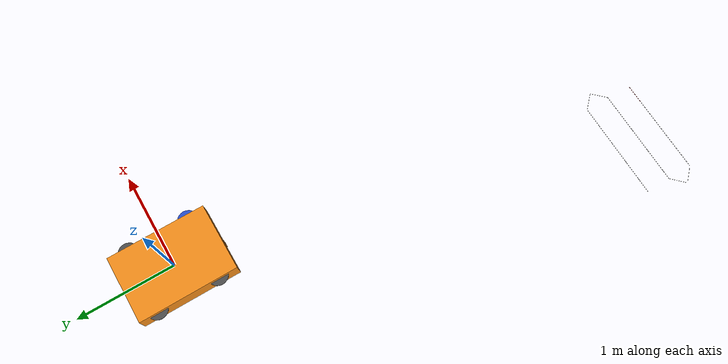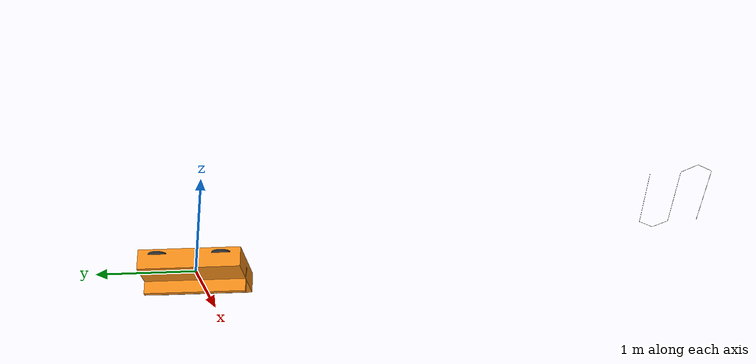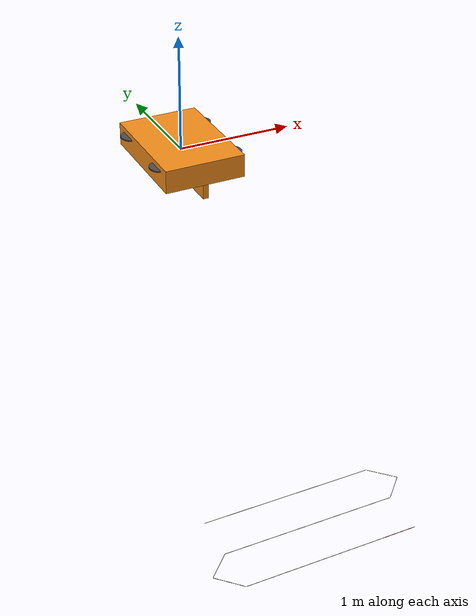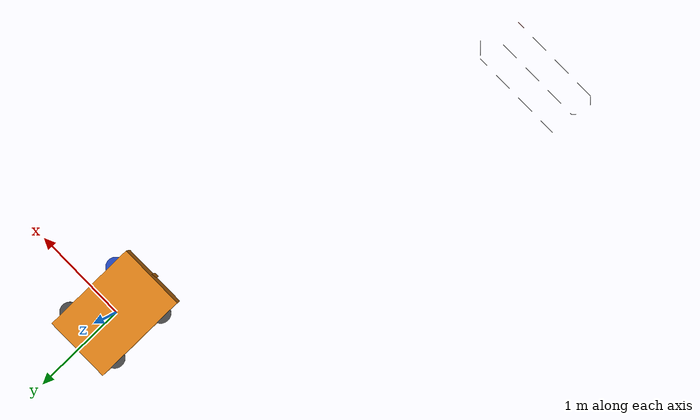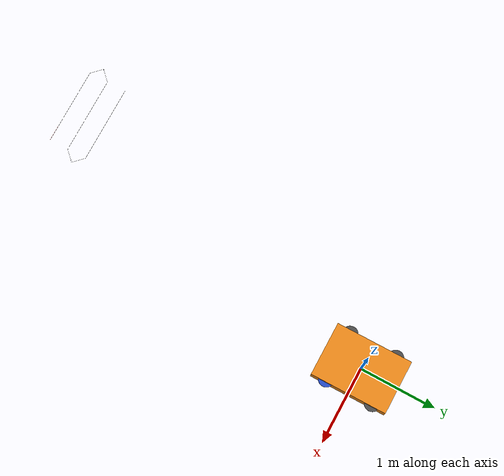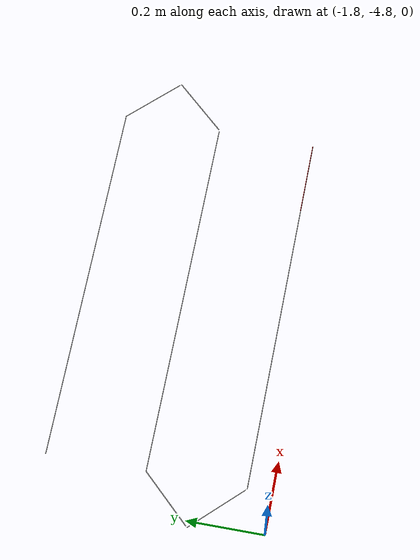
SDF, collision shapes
<?xml version='1.0'?>
<sdf version='1.5'>
  <model name='kitex_with_tether'>
    <include>
      <uri>model://kitex</uri>
    </include>
    <include>
      <uri>model://tether</uri>
    </include>
   </model>
</sdf>

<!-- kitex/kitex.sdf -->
<sdf version='1.6'>
	<model name='kitex'>
	<link name='base_link'>
		  <pose>0 0 0 0 -0 0</pose>
		  <inertial>
			<pose>0 0 -0.0 0 -0 0</pose>
			<mass>1.5</mass> <!-- [kg] -->
			<inertia> <!-- [kg/m²]-->
			  <ixx>0.15</ixx>
			  <ixy>0</ixy>
			  <ixz>0</ixz>
			  <iyy>0.05</iyy>
			  <iyz>0</iyz>
			  <izz>0.15</izz>
			</inertia>
		</inertial>
		<!-- TODO -->
		  <collision name='base_link_collision_wing'>
			<pose>0 0 -0.1 0 -0 0</pose>
			<geometry>
			  <box>
				<size>0.05 1 0.25</size>
			  </box>
			</geometry>
			<surface>
			  <contact>
				<ode>
				  <max_vel>10</max_vel>
				  <min_depth>0.01</min_depth>
				</ode>
			  </contact>
			</surface>
		  </collision>
		  <collision name='base_link_collision_mounts'>
			<pose>0 0 0 0 -0 0</pose>
			<geometry>
			  <box>
				<size>0.7 1.0 0.2</size>
			  </box>
			</geometry>
			<surface>
			  <contact>
				<ode>
				  <max_vel>10</max_vel>
				  <min_depth>0.01</min_depth>
				</ode>
			  </contact>
			</surface>
		</collision>
		<visual name='base_link_wing_visual'>
			<pose>0 0 0 0 -1.57 0</pose>
			<geometry>
			  <mesh>
				<scale>0.001 0.001 0.001</scale>
				<uri>model://kitex/meshes/quadkitex_main.dae</uri>
			  </mesh>
			</geometry>
			<material>
			  <script>
				<name>Gazebo/Orange</name>
				<uri>__default__</uri>
			  </script>
			</material>
		</visual>
		<visual name='base_link_core_visual'>
			<pose>0 0 -0.35 0 0 0</pose>
			<geometry>
			  <cylinder>
				<radius>0.01</radius>
				<length>0.7</length>
			  </cylinder>
			</geometry>
			<material>
			  <script>
				<name>Gazebo/Orange</name>
				<uri>__default__</uri>
			  </script>
			</material>
		</visual>
		<gravity>1</gravity>
		<velocity_decay/>
		<self_collide>0</self_collide>
	</link>

	<link name='rigid_wing/imu_link'>
	  <pose>0 0 0 0 -0 0</pose>
	  <inertial>
		<pose>0 0 0 0 -0 0</pose>
		<mass>0.015</mass>
		<inertia>
		  <ixx>1e-05</ixx>
		  <ixy>0</ixy>
		  <ixz>0</ixz>
		  <iyy>1e-05</iyy>
		  <iyz>0</iyz>
		  <izz>1e-05</izz>
		</inertia>
	  </inertial>
	</link>
	<joint name='rigid_wing/imu_joint' type='revolute'>
	  <child>rigid_wing/imu_link</child>
	  <parent>base_link</parent>
	  <axis>
		<xyz>1 0 0</xyz>
		<limit>
		  <lower>0</lower>
		  <upper>0</upper>
		  <effort>0</effort>
		  <velocity>0</velocity>
		</limit>
		<dynamics>
		  <spring_reference>0</spring_reference>
		  <spring_stiffness>0</spring_stiffness>
		</dynamics>
		<use_parent_model_frame>1</use_parent_model_frame>
	  </axis>
	</joint>

	<link name='rotor_0'>
		<pose>0.31 -0.31 0.05 0 -0 0</pose>
      <inertial>
		<pose>0 0 0 0 0 0</pose>
		<mass>0.005</mass>
        <inertia>
		  <ixx>9.75e-07</ixx>
          <ixy>0</ixy>
          <ixz>0</ixz>
		  <iyy>0.000166704</iyy>
          <iyz>0</iyz>
		  <izz>0.000167604</izz>
        </inertia>
      </inertial>
	  <collision name='rotor_0_collision'>
		<pose>0 0 0 0 -0 0</pose>
		<geometry>
		  <cylinder>
			<length>0.01</length>
			<radius>0.1</radius>
		  </cylinder>
		</geometry>
		<surface>
		  <contact>
			<ode/>
		  </contact>
		  <friction>
			<ode/>
		  </friction>
		</surface>
	  </collision>
	  <visual name='rotor_0_visual'>
		<pose>0 0 0 0 -0 0</pose>
		<geometry>
		  <mesh>
			<scale>0.5 0.5 0.5</scale>
			<uri>model://standard_vtol/meshes/iris_prop_ccw.dae</uri>
		  </mesh>
		</geometry>
		<material>
		  <script>
			<name>Gazebo/Blue</name>
			<uri>__default__</uri>
		  </script>
		</material>
	  </visual>
	  <gravity>1</gravity>
	  <velocity_decay/>
	  <self_collide>0</self_collide>
    </link>
	<joint name='rotor_0_joint' type='revolute'>
	  <child>rotor_0</child>
      <parent>base_link</parent>
      <axis>
		<xyz>0 0 1</xyz>
        <limit>
		  <lower>-1e+16</lower>
		  <upper>1e+16</upper>
        </limit>
        <dynamics>
          <spring_reference>0</spring_reference>
          <spring_stiffness>0</spring_stiffness>
        </dynamics>
        <use_parent_model_frame>1</use_parent_model_frame>
      </axis>
    </joint>

    <link name='rotor_1'>
		<pose>-0.31 0.31 0.05 0 -0 0</pose>
      <inertial>
        <pose>0 0 0 0 -0 0</pose>
        <mass>0.005</mass>
        <inertia>
          <ixx>9.75e-07</ixx>
          <ixy>0</ixy>
          <ixz>0</ixz>
          <iyy>0.000166704</iyy>
          <iyz>0</iyz>
          <izz>0.000167604</izz>
        </inertia>
      </inertial>
      <collision name='rotor_1_collision'>
        <pose>0 0 0 0 -0 0</pose>
        <geometry>
          <cylinder>
			<length>0.01</length>
			<radius>0.1</radius>
          </cylinder>
        </geometry>
        <surface>
          <contact>
            <ode/>
          </contact>
          <friction>
            <ode/>
          </friction>
        </surface>
      </collision>
      <visual name='rotor_1_visual'>
        <pose>0 0 0 0 -0 0</pose>
        <geometry>
          <mesh>
			<scale>0.5 0.5 0.5</scale>
			<uri>model://standard_vtol/meshes/iris_prop_ccw.dae</uri>
          </mesh>
        </geometry>
        <material>
          <script>
			<name>Gazebo/DarkGrey</name>
            <uri>__default__</uri>
          </script>
        </material>
      </visual>
      <gravity>1</gravity>
      <velocity_decay/>
      <self_collide>0</self_collide>
    </link>
    <joint name='rotor_1_joint' type='revolute'>
      <child>rotor_1</child>
      <parent>base_link</parent>
      <axis>
        <xyz>0 0 1</xyz>
        <limit>
          <lower>-1e+16</lower>
          <upper>1e+16</upper>
        </limit>
        <dynamics>
          <spring_reference>0</spring_reference>
          <spring_stiffness>0</spring_stiffness>
        </dynamics>
        <use_parent_model_frame>1</use_parent_model_frame>
      </axis>
    </joint>

    <link name='rotor_2'>
	  <pose>0.31 0.31 0.05 0 -0 0</pose>
      <inertial>
        <pose>0 0 0 0 -0 0</pose>
        <mass>0.005</mass>
        <inertia>
          <ixx>9.75e-07</ixx>
          <ixy>0</ixy>
          <ixz>0</ixz>
          <iyy>0.000166704</iyy>
          <iyz>0</iyz>
          <izz>0.000167604</izz>
        </inertia>
      </inertial>
      <collision name='rotor_2_collision'>
        <pose>0 0 0 0 -0 0</pose>
        <geometry>
          <cylinder>
			<length>0.01</length>
			<radius>0.1</radius>
          </cylinder>
        </geometry>
        <surface>
          <contact>
            <ode/>
          </contact>
          <friction>
            <ode/>
          </friction>
        </surface>
      </collision>
      <visual name='rotor_2_visual'>
        <pose>0 0 0 0 -0 0</pose>
        <geometry>
          <mesh>
			<scale>0.5 0.5 0.5</scale>
			<uri>model://standard_vtol/meshes/iris_prop_ccw.dae</uri>
          </mesh>
        </geometry>
        <material>
          <script>
            <name>Gazebo/DarkGrey</name>
            <uri>__default__</uri>
          </script>
        </material>
      </visual>
      <gravity>1</gravity>
      <velocity_decay/>
      <self_collide>0</self_collide>
    </link>
    <joint name='rotor_2_joint' type='revolute'>
      <child>rotor_2</child>
      <parent>base_link</parent>
      <axis>
        <xyz>0 0 1</xyz>
        <limit>
          <lower>-1e+16</lower>
          <upper>1e+16</upper>
        </limit>
        <dynamics>
          <spring_reference>0</spring_reference>
          <spring_stiffness>0</spring_stiffness>
        </dynamics>
        <use_parent_model_frame>1</use_parent_model_frame>
      </axis>
    </joint>

    <link name='rotor_3'>
	  <pose>-0.31 -0.31 0.05 0 -0 0</pose>
      <inertial>
		<pose>0 0 0 0 0 0</pose>
        <mass>0.005</mass>
        <inertia>
          <ixx>9.75e-07</ixx>
          <ixy>0</ixy>
          <ixz>0</ixz>
          <iyy>0.000166704</iyy>
          <iyz>0</iyz>
          <izz>0.000167604</izz>
        </inertia>
      </inertial>
      <collision name='rotor_3_collision'>
        <pose>0 0 0 0 -0 0</pose>
        <geometry>
          <cylinder>
			<length>0.01</length>
			<radius>0.1</radius>
          </cylinder>
        </geometry>
        <surface>
          <contact>
            <ode/>
          </contact>
          <friction>
            <ode/>
          </friction>
        </surface>
      </collision>
      <visual name='rotor_3_visual'>
        <pose>0 0 0 0 -0 0</pose>
        <geometry>
          <mesh>
			<scale>0.5 0.5 0.5</scale>
			<uri>model://standard_vtol/meshes/iris_prop_ccw.dae</uri>
          </mesh>
        </geometry>
        <material>
          <script>
            <name>Gazebo/DarkGrey</name>
            <uri>__default__</uri>
          </script>
        </material>
      </visual>
      <gravity>1</gravity>
      <velocity_decay/>
      <self_collide>0</self_collide>
    </link>
    <joint name='rotor_3_joint' type='revolute'>
      <child>rotor_3</child>
      <parent>base_link</parent>
      <axis>
        <xyz>0 0 1</xyz>
        <limit>
          <lower>-1e+16</lower>
          <upper>1e+16</upper>
        </limit>
        <dynamics>
          <spring_reference>0</spring_reference>
          <spring_stiffness>0</spring_stiffness>
        </dynamics>
        <use_parent_model_frame>1</use_parent_model_frame>
      </axis>
    </joint>

	<link name="rudder">
		<pose>0 0 -0.7 0 0 0</pose>
      <inertial>
        <mass>0.00000001</mass>
        <inertia>
          <ixx>0.000001</ixx>
          <ixy>0.0</ixy>
          <iyy>0.000001</iyy>
          <ixz>0.0</ixz>
          <iyz>0.0</iyz>
          <izz>0.000001</izz>
        </inertia>
      </inertial>
	  <visual name='rudder_visual'>
		<pose>0 0 0 0 0 1.57</pose>
		<geometry>
		  <mesh>
			<scale>0.001 0.001 0.001</scale>
			<uri>model://kitex/meshes/rudderkitex.dae</uri>
		  </mesh>
		</geometry>
		<material>
		  <script>
			<name>Gazebo/Blue</name>
			<uri>__default__</uri>
		  </script>
		</material>
	  </visual>
    </link>
	<joint name='rudder_joint' type='revolute'>
      <parent>base_link</parent>
	  <child>rudder</child>
	  <pose>0.005 0.005 0 0 -0 0</pose>
      <axis>
		<xyz>1 0 0</xyz>
        <limit>
          <!-- -30/+30 deg. -->
          <lower>-0.53</lower>
          <upper>0.53</upper>
        </limit>
        <dynamics>
          <damping>1.000</damping>
        </dynamics>
      </axis>
      <physics>
        <ode>
          <implicit_spring_damper>1</implicit_spring_damper>
        </ode>
      </physics>
  </joint>

	<link name="elevator">
	<pose>0 0 -.63 0 0 0</pose>
	  <inertial>
		<mass>0.00000001</mass>
		<inertia>
		  <ixx>0.000001</ixx>
		  <ixy>0.0</ixy>
		  <iyy>0.000001</iyy>
		  <ixz>0.0</ixz>
		  <iyz>0.0</iyz>
		  <izz>0.000001</izz>
		</inertia>
		<pose>0 0 0 0 -0 0</pose>
	  </inertial>
	  <visual name='elevator_visual'>
		<pose>0 0 0 -1.57 -1.57 1.57</pose>
		<geometry>
		  <mesh>
			<scale>0.001 0.001 0.0005</scale>
			<uri>model://kitex/meshes/elevatorkitex.dae</uri>
		  </mesh>
		</geometry>
		<material>
		  <script>
			<name>Gazebo/Blue</name>
			<uri>__default__</uri>
		  </script>
		</material>
	  </visual>
	</link>
	<joint name='elevator_joint' type='revolute'>
      <parent>base_link</parent>
	  <child>elevator</child>
	  <pose> 0 0 0 0 -0 0</pose>
      <axis>
        <xyz>0 1 0</xyz>
        <limit>
          <!-- -40/+40 deg. -->
		  <upper>-1.117</upper>
		  <lower>0.304</lower>
        </limit>
        <dynamics>
          <damping>1.000</damping>
        </dynamics>
      </axis>
      <physics>
        <ode>
          <implicit_spring_damper>1</implicit_spring_damper>
        </ode>
      </physics>
    </joint>

    <!-- KiteX model: Main wing - Left -->
    <!-- profile: Selig 8037
	   cord:    100 mm
	   span:    1400/2=700 mm
	   thickness 20 mm -->
	<plugin name="left_wing" filename="libLiftDragPlugin.so">
	<robotNamespace></robotNamespace>
	  <a0>0.087</a0><!-- 5 deg incidence -->
	  <cla>3.295</cla>
      <cda>0.166</cda>
      <cma>0.281</cma>
      <alpha_stall>0.305</alpha_stall>
      <cla_stall>-0.802</cla_stall>
      <cda_stall>-0.808</cda_stall>
      <cma_stall>-0.229</cma_stall>
	  <cp>0 -0.35 0</cp>
	  <area>0.014</area>
      <air_density>1.2041</air_density>
      <forward>0 0 1</forward>
	  <upward>1 0 0</upward>
      <link_name>base_link</link_name>
    </plugin>

	<!-- KiteX model: Main wing - Right -->
    <!-- profile: Selig 8037
	   cord:    100 mm
	   span:    1400/2=700 mm
	   thickness 20 mm -->
    <plugin name="right_wing" filename="libLiftDragPlugin.so">
      <robotNamespace></robotNamespace>
	  <a0>0.087</a0><!-- 5 deg incidence -->
	  <cla>3.295</cla>
      <cda>0.166</cda>
      <cma>0.281</cma>
      <alpha_stall>0.305</alpha_stall>
      <cla_stall>-0.802</cla_stall>
      <cda_stall>-0.808</cda_stall>
      <cma_stall>-0.229</cma_stall>
      <cp>0 0.35 0</cp>
	  <area>0.014</area>
      <air_density>1.2041</air_density>
      <forward>0 0 1</forward>
	  <upward>1 0 0</upward>
      <link_name>base_link</link_name>
    </plugin>

	<!-- KiteX model: Elevator -->
    <!-- profile: NACA 0012
	   cord:     60 mm
	   span:    600 mm
	   thickness 10 mm -->
	<plugin name="elevator" filename="libLiftDragPlugin.so">
		<robotNamespace></robotNamespace>
	<!-- http://airfoiltools.com/polar/details?polar=xf-n0012-il-500000 -->
      <a0>0</a0>
	  <cla>4.475</cla>
	  <cda>0.384</cda>
	  <cma>0.069</cma>
	  <alpha_stall>0.218</alpha_stall>
	  <cla_stall>-7.529</cla_stall>
	  <cda_stall>2.503</cda_stall>
	  <cma_stall>1.851</cma_stall>
	  <cp>0 0 0.63</cp>
	  <area>0.006</area>
	<!-- start: same as tailsitter -->
	  <air_density>1.2041</air_density>
	  <forward>0 0 1</forward>
	<!-- end: same as tailsitter -->
	  <upward>1 0 0</upward>
	  <link_name>base_link</link_name>
	<!-- start: same as tailsitter -->
	  <control_joint_name>
		elevator_joint
	  </control_joint_name>
	<!-- end: same as tailsitter -->
	</plugin>

  <!-- KiteX model: Rudder -->
  <!-- profile: NACA 0012
	   cord:     60 mm
	   span:    600 mm
	   thickness 10 mm -->
	<plugin name="rudder" filename="libLiftDragPlugin.so">
	  <robotNamespace></robotNamespace>
	<!-- http://airfoiltools.com/polar/details?polar=xf-n0012-il-500000 -->
      <a0>0</a0>
	  <cla>4.475</cla>
	  <cda>0.384</cda>
	  <cma>0.069</cma>
	  <alpha_stall>0.218</alpha_stall>
	  <cla_stall>-7.529</cla_stall>
	  <cda_stall>2.503</cda_stall>
	  <cma_stall>1.851</cma_stall>
	  <cp>0 0 0.7</cp>
	  <area>0.006</area>
	  <air_density>1.2041</air_density>
	  <forward>0 0 1</forward>
	  <upward>0 1 0</upward>
	  <link_name>base_link</link_name>
	</plugin>

	<!-- KiteX model: Vertical wing Left -->
    <!-- profile: Selig 8037
	   cord:    100 mm
	   span:    800 mm
	   thickness 20 mm -->
	<plugin name="V-wing-left" filename="libLiftDragPlugin.so">
		<robotNamespace></robotNamespace>
	<!-- http://airfoiltools.com/polar/details?polar=xf-s8037-il-200000 -->
	<a0>0.14</a0> <!-- 8 deg positive -->
	  <cla>3.295</cla>
      <cda>0.166</cda>
      <cma>0.281</cma>
      <alpha_stall>0.305</alpha_stall>
      <cla_stall>-0.802</cla_stall>
      <cda_stall>-0.808</cda_stall>
      <cma_stall>-0.229</cma_stall>
	  <cp>0 -0.2 0</cp>
	  <area>0.016</area>
	<!-- start: same as tailsitter -->
	  <air_density>1.2041</air_density>
	  <forward>0 0 1</forward>
	<!-- end: same as tailsitter -->
	  <upward>0 -1 0</upward>
	  <link_name>base_link</link_name>
	</plugin>

	<!-- KiteX model: Vertical wing  Right -->
    <!-- profile: Selig 8038
	   cord:    100 mm
	   span:    800 mm
	   thickness 20 mm -->
	<plugin name="V-wing-right" filename="libLiftDragPlugin.so">
	  <robotNamespace></robotNamespace>
	<!-- http://airfoiltools.com/polar/details?polar=xf-s8037-il-200000 -->
	<a0>0.14</a0> <!-- 8 deg positive -->
	  <cla>3.295</cla>
      <cda>0.166</cda>
      <cma>0.281</cma>
      <alpha_stall>0.305</alpha_stall>
      <cla_stall>-0.802</cla_stall>
      <cda_stall>-0.808</cda_stall>
      <cma_stall>-0.229</cma_stall>
	  <cp>0 0.2 0</cp>
	  <area>0.016</area>
	<!-- start: same as tailsitter -->
	  <air_density>1.2041</air_density>
	  <forward>0 0 1</forward>
	<!-- end: same as tailsitter -->
	  <upward>0 -1 0</upward>
	  <link_name>base_link</link_name>
	</plugin>

	<!-- KiteX Motors -->
	<plugin name='m0_motor_model' filename='librotors_gazebo_motor_model.so'>
	  <robotNamespace></robotNamespace>
	  <jointName>rotor_0_joint</jointName>
	  <linkName>rotor_0</linkName>
	  <turningDirection>ccw</turningDirection>
	  <timeConstantUp>0.0125</timeConstantUp>
	  <timeConstantDown>0.025</timeConstantDown>
	  <maxRotVelocity>576</maxRotVelocity> <!-- rad/s -->
	  <motorConstant>0.00001824</motorConstant><!-- N/(rad/s)² -->
	  <momentConstant>0.06</momentConstant>
	  <commandSubTopic>/gazebo/command/motor_speed</commandSubTopic>
	  <motorNumber>0</motorNumber>
	  <rotorDragCoefficient>8.06428e-5</rotorDragCoefficient>
      <rollingMomentCoefficient>1e-06</rollingMomentCoefficient>
      <motorSpeedPubTopic>/motor_speed/0</motorSpeedPubTopic>
      <rotorVelocitySlowdownSim>10</rotorVelocitySlowdownSim>
    </plugin>

	<plugin name='m1_motor_model' filename='librotors_gazebo_motor_model.so'>
	  <robotNamespace></robotNamespace>
	  <jointName>rotor_1_joint</jointName>
	  <linkName>rotor_1</linkName>
	  <turningDirection>ccw</turningDirection>
	  <timeConstantUp>0.0125</timeConstantUp>
	  <timeConstantDown>0.025</timeConstantDown>
	  <maxRotVelocity>576</maxRotVelocity> <!-- rad/s -->
	  <motorConstant>0.00001824</motorConstant><!-- N/(rad/s)² -->
	  <momentConstant>0.06</momentConstant>
	  <commandSubTopic>/gazebo/command/motor_speed</commandSubTopic>
	  <motorNumber>1</motorNumber>
	  <rotorDragCoefficient>8.06428e-5</rotorDragCoefficient>
      <rollingMomentCoefficient>1e-06</rollingMomentCoefficient>
      <motorSpeedPubTopic>/motor_speed/1</motorSpeedPubTopic>
      <rotorVelocitySlowdownSim>10</rotorVelocitySlowdownSim>
    </plugin>

	<plugin name='m2_motor_model' filename='librotors_gazebo_motor_model.so'>
	  <robotNamespace></robotNamespace>
	  <jointName>rotor_2_joint</jointName>
	  <linkName>rotor_2</linkName>
	  <turningDirection>cw</turningDirection>
	  <timeConstantUp>0.0125</timeConstantUp>
	  <timeConstantDown>0.025</timeConstantDown>
	  <maxRotVelocity>576</maxRotVelocity> <!-- rad/s -->
	  <motorConstant>0.00001824</motorConstant><!-- N/(rad/s)² -->
	  <momentConstant>0.06</momentConstant>
	  <commandSubTopic>/gazebo/command/motor_speed</commandSubTopic>
	  <motorNumber>2</motorNumber>
	  <rotorDragCoefficient>8.06428e-5</rotorDragCoefficient>
	  <rollingMomentCoefficient>1e-06</rollingMomentCoefficient>
	  <motorSpeedPubTopic>/motor_speed/2</motorSpeedPubTopic>
	  <rotorVelocitySlowdownSim>10</rotorVelocitySlowdownSim>
	</plugin>

	<plugin name='m3_motor_model' filename='librotors_gazebo_motor_model.so'>
	  <robotNamespace></robotNamespace>
	  <jointName>rotor_3_joint</jointName>
	  <linkName>rotor_3</linkName>
	  <turningDirection>cw</turningDirection>
	  <timeConstantUp>0.0125</timeConstantUp>
	  <timeConstantDown>0.025</timeConstantDown>
	  <maxRotVelocity>576</maxRotVelocity> <!--  rad/s -->
	  <motorConstant>0.00001824</motorConstant><!-- N/(rad/s)² -->
	  <momentConstant>0.06</momentConstant>
	  <commandSubTopic>/gazebo/command/motor_speed</commandSubTopic>
	  <motorNumber>3</motorNumber>
	  <rotorDragCoefficient>8.06428e-5</rotorDragCoefficient>
	  <rollingMomentCoefficient>1e-06</rollingMomentCoefficient>
	  <motorSpeedPubTopic>/motor_speed/3</motorSpeedPubTopic>
	  <rotorVelocitySlowdownSim>10</rotorVelocitySlowdownSim>
	</plugin>

    <plugin name='rotors_gazebo_imu_plugin' filename='librotors_gazebo_imu_plugin.so'>
      <robotNamespace></robotNamespace>
      <linkName>rigid_wing/imu_link</linkName>
      <imuTopic>/imu</imuTopic>
      <gyroscopeNoiseDensity>0.0003394</gyroscopeNoiseDensity>
      <gyroscopeRandomWalk>3.8785e-05</gyroscopeRandomWalk>
      <gyroscopeBiasCorrelationTime>1000.0</gyroscopeBiasCorrelationTime>
      <gyroscopeTurnOnBiasSigma>0.0087</gyroscopeTurnOnBiasSigma>
      <accelerometerNoiseDensity>0.004</accelerometerNoiseDensity>
      <accelerometerRandomWalk>0.006</accelerometerRandomWalk>
      <accelerometerBiasCorrelationTime>300.0</accelerometerBiasCorrelationTime>
      <accelerometerTurnOnBiasSigma>0.196</accelerometerTurnOnBiasSigma>
    </plugin>

	<plugin name='wind_field_plugin' filename='libgazebo_wind_field_plugin.so'>
	  <robotNamespace></robotNamespace>
	  <frameId>base_link</frameId>
	  <linkName>base_link</linkName>
	  <windAzimuth>3.14</windAzimuth>
	  <windVelocityMean>8</windVelocityMean>
	  <windGustAzimuth>0</windGustAzimuth>
	  <windGustDuration>0</windGustDuration>
	  <windGustStart>0</windGustStart>
	  <windGustVelocityMean>0</windGustVelocityMean>
	</plugin>

	<plugin name='mavlink_interface' filename='librotors_gazebo_mavlink_interface.so'>
	  <robotNamespace></robotNamespace>
	  <imuSubTopic>/imu</imuSubTopic>
	  <motorSpeedCommandPubTopic>/gazebo/command/motor_speed</motorSpeedCommandPubTopic>
	  <control_channels>
		<channel name="rotor0">
		  <input_index>0</input_index>
		  <input_offset>0</input_offset>
		  <input_scaling>1200</input_scaling>
		  <zero_position_disarmed>0</zero_position_disarmed>
		  <zero_position_armed>0</zero_position_armed>
		  <joint_control_type>velocity</joint_control_type>
		  <joint_name>rotor_0_joint</joint_name>
		</channel>
		<channel name="rotor1">
		  <input_index>1</input_index>
		  <input_offset>0</input_offset>
		  <input_scaling>1200</input_scaling>
		  <zero_position_disarmed>0</zero_position_disarmed>
		  <zero_position_armed>0</zero_position_armed>
		  <joint_control_type>velocity</joint_control_type>
		  <joint_name>rotor_1_joint</joint_name>
		</channel>
		<channel name="rotor2">
		  <input_index>2</input_index>
		  <input_offset>0</input_offset>
		  <input_scaling>1200</input_scaling>
		  <zero_position_disarmed>0</zero_position_disarmed>
		  <zero_position_armed>0</zero_position_armed>
		  <joint_control_type>velocity</joint_control_type>
		  <joint_name>rotor_2_joint</joint_name>
		</channel>
		<channel name="rotor3">
		  <input_index>3</input_index>
		  <input_offset>0</input_offset>
		  <input_scaling>1200</input_scaling>
		  <zero_position_disarmed>0</zero_position_disarmed>
		  <zero_position_armed>0</zero_position_armed>
		  <joint_control_type>velocity</joint_control_type>
		  <joint_name>rotor_3_joint</joint_name>
		</channel>
		<channel name="rudder">
		  <input_index>4</input_index>
		  <input_offset>0</input_offset>
		  <input_scaling>1</input_scaling>
		  <zero_position_disarmed>0</zero_position_disarmed>
		  <zero_position_armed>-0.525</zero_position_armed>
		  <joint_control_type>position_kinematic</joint_control_type>
		  <joint_name>rudder_joint</joint_name>
		</channel>
		<channel name="elevator">
		  <input_index>5</input_index>
		  <input_offset>0</input_offset>
		  <input_scaling>1</input_scaling>
		  <zero_position_disarmed>0</zero_position_disarmed>
		  <zero_position_armed>0</zero_position_armed>
		  <joint_control_type>position_kinematic</joint_control_type>
		  <joint_name>elevator_joint</joint_name>
		</channel>
      </control_channels>
    </plugin>
     <static>0</static>
  </model>
</sdf>

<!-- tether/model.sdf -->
<sdf version="1.5">
  <model name="tether">
    <pose>-1.81 -4.23 0.055 0 0 0</pose>
    <link name="link_00">
      <gravity>true</gravity>
      <pose>0.1 0 0 0 0 0</pose>
      <inertial>
        <mass>0.009</mass>
        <pose>0.1 0 0 0 0 0</pose>
        <inertia>
          <ixx>0.01</ixx>
          <ixy>0</ixy>
          <ixz>0</ixz>
          <iyy>0.01</iyy>
          <iyz>0</iyz>
          <izz>0.01</izz>
        </inertia>
      </inertial>
      <visual name="sphere">
        <geometry>
          <sphere>
            <radius>0.009</radius>
          </sphere>
        </geometry>
        <material>
	  <script>
            <name>Gazebo/Red</name>
            <uri>file://media/materials/scripts/gazebo.material</uri>
          </script>
        </material>
      </visual>
    </link>
    <link name="link_01">
      <gravity>true</gravity>
      <pose>0.1 0 0 0 0 0</pose>
      <inertial>
        <mass>0.009</mass>
        <pose>0.1 0 0 0 0 0</pose>
        <inertia>
          <ixx>0.01</ixx>
          <ixy>0</ixy>
          <ixz>0</ixz>
          <iyy>0.01</iyy>
          <iyz>0</iyz>
          <izz>0.01</izz>
        </inertia>
      </inertial>
      <collision name="collision">
        <pose>0.1 0 0 0 1.570790 0</pose>
        <geometry>
          <cylinder>
            <length>0.2</length>
            <radius>0.001</radius>
          </cylinder>
        </geometry>
        <surface>
          <contact>
            <ode>
              <min_depth>0.00005</min_depth>
            </ode>
          </contact>
          <friction>
            <ode>
              <mu>1.0</mu>
              <mu2>1.0</mu2>
            </ode>
          </friction>
        </surface>
      </collision>
      <visual name="visual">
        <pose>0.1 0 0 0 1.570790 0</pose>
        <geometry>
          <cylinder>
            <length>0.2</length>
            <radius>0.001</radius>
          </cylinder>
        </geometry>
	<material>
	  <script>
            <name>Gazebo/White</name>
            <uri>file://media/materials/scripts/gazebo.material</uri>
          </script>
        </material>
      </visual>
    </link>
    <link name="link_02">
      <gravity>true</gravity>
      <pose>0.3 0 0 0 0 0</pose>
      <inertial>
        <mass>0.009</mass>
        <pose>0.1 0 0 0 0 0</pose>
        <inertia>
          <ixx>0.01</ixx>
          <ixy>0</ixy>
          <ixz>0</ixz>
          <iyy>0.01</iyy>
          <iyz>0</iyz>
          <izz>0.01</izz>
        </inertia>
      </inertial>
      <collision name="collision">
        <pose>0.1 0 0 0 1.570790 0</pose>
        <geometry>
          <cylinder>
            <length>0.2</length>
            <radius>0.001</radius>
          </cylinder>
        </geometry>
        <surface>
          <contact>
            <ode>
              <min_depth>0.00005</min_depth>
            </ode>
          </contact>
          <friction>
            <ode>
              <mu>1.0</mu>
              <mu2>1.0</mu2>
            </ode>
          </friction>
        </surface>
      </collision>
      <visual name="visual">
        <pose>0.1 0 0 0 1.570790 0</pose>
        <geometry>
          <cylinder>
            <length>0.2</length>
            <radius>0.001</radius>
          </cylinder>
        </geometry>
	<material>
	  <script>
            <name>Gazebo/White</name>
            <uri>file://media/materials/scripts/gazebo.material</uri>
          </script>
        </material>
      </visual>
      <visual name="sphere">
        <geometry>
          <sphere>
            <radius>0.009</radius>
          </sphere>
        </geometry>
        <material>
	  <script>
            <name>Gazebo/Red</name>
            <uri>file://media/materials/scripts/gazebo.material</uri>
          </script>
        </material>
      </visual>
    </link>
    <link name="link_03">
      <gravity>true</gravity>
      <pose>0.5 0 0 0 0 0</pose>
      <inertial>
        <mass>0.009</mass>
        <pose>0.1 0 0 0 0 0</pose>
        <inertia>
          <ixx>0.01</ixx>
          <ixy>0</ixy>
          <ixz>0</ixz>
          <iyy>0.01</iyy>
          <iyz>0</iyz>
          <izz>0.01</izz>
        </inertia>
      </inertial>
      <collision name="collision">
        <pose>0.1 0 0 0 1.570790 0</pose>
        <geometry>
          <cylinder>
            <length>0.2</length>
            <radius>0.001</radius>
          </cylinder>
        </geometry>
        <surface>
          <contact>
            <ode>
              <min_depth>0.00005</min_depth>
            </ode>
          </contact>
          <friction>
            <ode>
              <mu>1.0</mu>
              <mu2>1.0</mu2>
            </ode>
          </friction>
        </surface>
      </collision>
      <visual name="visual">
        <pose>0.1 0 0 0 1.570790 0</pose>
        <geometry>
          <cylinder>
            <length>0.2</length>
            <radius>0.001</radius>
          </cylinder>
        </geometry>
	<material>
	  <script>
            <name>Gazebo/White</name>
            <uri>file://media/materials/scripts/gazebo.material</uri>
          </script>
        </material>
      </visual>
      <visual name="sphere">
        <geometry>
          <sphere>
            <radius>0.009</radius>
          </sphere>
        </geometry>
        <material>
	  <script>
            <name>Gazebo/Red</name>
            <uri>file://media/materials/scripts/gazebo.material</uri>
          </script>
        </material>
      </visual>
    </link>
    <link name="link_04">
      <gravity>true</gravity>
      <pose>0.7 0 0 0 0 0</pose>
      <inertial>
        <mass>0.009</mass>
        <pose>0.1 0 0 0 0 0</pose>
        <inertia>
          <ixx>0.01</ixx>
          <ixy>0</ixy>
          <ixz>0</ixz>
          <iyy>0.01</iyy>
          <iyz>0</iyz>
          <izz>0.01</izz>
        </inertia>
      </inertial>
      <collision name="collision">
        <pose>0.1 0 0 0 1.570790 0</pose>
        <geometry>
          <cylinder>
            <length>0.2</length>
            <radius>0.001</radius>
          </cylinder>
        </geometry>
        <surface>
          <contact>
            <ode>
              <min_depth>0.00005</min_depth>
            </ode>
          </contact>
          <friction>
            <ode>
              <mu>1.0</mu>
              <mu2>1.0</mu2>
            </ode>
          </friction>
        </surface>
      </collision>
      <visual name="visual">
        <pose>0.1 0 0 0 1.570790 0</pose>
        <geometry>
          <cylinder>
            <length>0.2</length>
            <radius>0.001</radius>
          </cylinder>
        </geometry>
	<material>
	  <script>
            <name>Gazebo/White</name>
            <uri>file://media/materials/scripts/gazebo.material</uri>
          </script>
        </material>
      </visual>
      <visual name="sphere">
        <geometry>
          <sphere>
            <radius>0.009</radius>
          </sphere>
        </geometry>
        <material>
	  <script>
            <name>Gazebo/Red</name>
            <uri>file://media/materials/scripts/gazebo.material</uri>
          </script>
        </material>
      </visual>
    </link>
    <link name="link_05">
      <gravity>true</gravity>
      <pose>0.9 0 0 0 0 0</pose>
      <inertial>
        <mass>0.009</mass>
        <pose>0.1 0 0 0 0 0</pose>
        <inertia>
          <ixx>0.01</ixx>
          <ixy>0</ixy>
          <ixz>0</ixz>
          <iyy>0.01</iyy>
          <iyz>0</iyz>
          <izz>0.01</izz>
        </inertia>
      </inertial>
      <collision name="collision">
        <pose>0.1 0 0 0 1.570790 0</pose>
        <geometry>
          <cylinder>
            <length>0.2</length>
            <radius>0.001</radius>
          </cylinder>
        </geometry>
        <surface>
          <contact>
            <ode>
              <min_depth>0.00005</min_depth>
            </ode>
          </contact>
          <friction>
            <ode>
              <mu>1.0</mu>
              <mu2>1.0</mu2>
            </ode>
          </friction>
        </surface>
      </collision>
      <visual name="visual">
        <pose>0.1 0 0 0 1.570790 0</pose>
        <geometry>
          <cylinder>
            <length>0.2</length>
            <radius>0.001</radius>
          </cylinder>
        </geometry>
	<material>
	  <script>
            <name>Gazebo/White</name>
            <uri>file://media/materials/scripts/gazebo.material</uri>
          </script>
        </material>
      </visual>
      <visual name="sphere">
        <geometry>
          <sphere>
            <radius>0.009</radius>
          </sphere>
        </geometry>
        <material>
	  <script>
            <name>Gazebo/Red</name>
            <uri>file://media/materials/scripts/gazebo.material</uri>
          </script>
        </material>
      </visual>
    </link>
    <link name="link_06">
      <gravity>true</gravity>
      <pose>1.1 0 0 0 0 -.785</pose>
      <inertial>
        <mass>0.009</mass>
        <pose>0.0875 0 0 0 0 0</pose>
        <inertia>
          <ixx>0.01</ixx>
          <ixy>0</ixy>
          <ixz>0</ixz>
          <iyy>0.01</iyy>
          <iyz>0</iyz>
          <izz>0.01</izz>
        </inertia>
      </inertial>
      <collision name="collision">
        <pose>0.0875 0 0 0 1.570790 0</pose>
        <geometry>
          <cylinder>
            <length>0.175</length>
            <radius>0.001</radius>
          </cylinder>
        </geometry>
        <surface>
          <contact>
            <ode>
              <min_depth>0.00005</min_depth>
            </ode>
          </contact>
          <friction>
            <ode>
              <mu>1.0</mu>
              <mu2>1.0</mu2>
            </ode>
          </friction>
        </surface>
      </collision>
      <visual name="visual">
        <pose>0.0875 0 0 0 1.570790 0</pose>
        <geometry>
          <cylinder>
            <length>0.175</length>
            <radius>0.001</radius>
          </cylinder>
        </geometry>
	<material>
	  <script>
            <name>Gazebo/White</name>
            <uri>file://media/materials/scripts/gazebo.material</uri>
          </script>
        </material>
      </visual>
      <visual name="sphere">
        <geometry>
          <sphere>
            <radius>0.009</radius>
          </sphere>
        </geometry>
        <material>
	  <script>
            <name>Gazebo/Red</name>
            <uri>file://media/materials/scripts/gazebo.material</uri>
          </script>
        </material>
      </visual>
    </link>
    <link name="link_07">
      <gravity>true</gravity>
      <pose>1.227 -.127 0 0 0 -2.3415</pose>
      <inertial>
        <mass>0.009</mass>
        <pose>0.0875 0 0 0 0 0</pose>
        <inertia>
          <ixx>0.01</ixx>
          <ixy>0</ixy>
          <ixz>0</ixz>
          <iyy>0.01</iyy>
          <iyz>0</iyz>
          <izz>0.01</izz>
        </inertia>
      </inertial>
      <collision name="collision">
        <pose>0.0875 0 0 0 1.570790 0</pose>
        <geometry>
          <cylinder>
            <length>0.175</length>
            <radius>0.001</radius>
          </cylinder>
        </geometry>
        <surface>
          <contact>
            <ode>
              <min_depth>0.00005</min_depth>
            </ode>
          </contact>
          <friction>
            <ode>
              <mu>1.0</mu>
              <mu2>1.0</mu2>
            </ode>
          </friction>
        </surface>
      </collision>
      <visual name="visual">
        <pose>0.0875 0 0 0 1.570790 0</pose>
        <geometry>
          <cylinder>
            <length>0.175</length>
            <radius>0.001</radius>
          </cylinder>
        </geometry>
	<material>
	  <script>
            <name>Gazebo/White</name>
            <uri>file://media/materials/scripts/gazebo.material</uri>
          </script>
        </material>
      </visual>
      <visual name="sphere">
        <geometry>
          <sphere>
            <radius>0.009</radius>
          </sphere>
        </geometry>
        <material>
	  <script>
            <name>Gazebo/Red</name>
            <uri>file://media/materials/scripts/gazebo.material</uri>
          </script>
        </material>
      </visual>
    </link>
    <link name="link_08">
      <gravity>true</gravity>
      <pose>1.1 -.254 0 0 0 -3.1415</pose>
      <inertial>
        <mass>0.009</mass>
        <pose>0.1 0 0 0 0 0</pose>
        <inertia>
          <ixx>0.01</ixx>
          <ixy>0</ixy>
          <ixz>0</ixz>
          <iyy>0.01</iyy>
          <iyz>0</iyz>
          <izz>0.01</izz>
        </inertia>
      </inertial>
      <collision name="collision">
        <pose>0.1 0 0 0 1.570790 0</pose>
        <geometry>
          <cylinder>
            <length>0.2</length>
            <radius>0.001</radius>
          </cylinder>
        </geometry>
        <surface>
          <contact>
            <ode>
              <min_depth>0.00005</min_depth>
            </ode>
          </contact>
          <friction>
            <ode>
              <mu>1.0</mu>
              <mu2>1.0</mu2>
            </ode>
          </friction>
        </surface>
      </collision>
      <visual name="visual">
        <pose>0.1 0 0 0 1.570790 0</pose>
        <geometry>
          <cylinder>
            <length>0.2</length>
            <radius>0.001</radius>
          </cylinder>
        </geometry>
	<material>
	  <script>
            <name>Gazebo/White</name>
            <uri>file://media/materials/scripts/gazebo.material</uri>
          </script>
        </material>
      </visual>
      <visual name="sphere">
        <geometry>
          <sphere>
            <radius>0.009</radius>
          </sphere>
        </geometry>
        <material>
	  <script>
            <name>Gazebo/Red</name>
            <uri>file://media/materials/scripts/gazebo.material</uri>
          </script>
        </material>
      </visual>
    </link>
    <link name="link_09">
      <gravity>true</gravity>
      <pose>0.9 -.254 0 0 0 -3.1415</pose>
      <inertial>
        <mass>0.009</mass>
        <pose>0.1 0 0 0 0 0</pose>
        <inertia>
          <ixx>0.01</ixx>
          <ixy>0</ixy>
          <ixz>0</ixz>
          <iyy>0.01</iyy>
          <iyz>0</iyz>
          <izz>0.01</izz>
        </inertia>
      </inertial>
      <collision name="collision">
        <pose>0.1 0 0 0 1.570790 0</pose>
        <geometry>
          <cylinder>
            <length>0.2</length>
            <radius>0.001</radius>
          </cylinder>
        </geometry>
        <surface>
          <contact>
            <ode>
              <min_depth>0.00005</min_depth>
            </ode>
          </contact>
          <friction>
            <ode>
              <mu>1.0</mu>
              <mu2>1.0</mu2>
            </ode>
          </friction>
        </surface>
      </collision>
      <visual name="visual">
        <pose>0.1 0 0 0 1.570790 0</pose>
        <geometry>
          <cylinder>
            <length>0.2</length>
            <radius>0.001</radius>
          </cylinder>
        </geometry>
	<material>
	  <script>
            <name>Gazebo/White</name>
            <uri>file://media/materials/scripts/gazebo.material</uri>
          </script>
        </material>
      </visual>
      <visual name="sphere">
        <geometry>
          <sphere>
            <radius>0.009</radius>
          </sphere>
        </geometry>
        <material>
	  <script>
            <name>Gazebo/Red</name>
            <uri>file://media/materials/scripts/gazebo.material</uri>
          </script>
        </material>
      </visual>
    </link>
    <link name="link_10">
      <gravity>true</gravity>
      <pose>0.7 -.254 0 0 0 -3.1415</pose>
      <inertial>
        <mass>0.009</mass>
        <pose>0.1 0 0 0 0 0</pose>
        <inertia>
          <ixx>0.01</ixx>
          <ixy>0</ixy>
          <ixz>0</ixz>
          <iyy>0.01</iyy>
          <iyz>0</iyz>
          <izz>0.01</izz>
        </inertia>
      </inertial>
      <collision name="collision">
        <pose>0.1 0 0 0 1.570790 0</pose>
        <geometry>
          <cylinder>
            <length>0.2</length>
            <radius>0.001</radius>
          </cylinder>
        </geometry>
        <surface>
          <contact>
            <ode>
              <min_depth>0.00005</min_depth>
            </ode>
          </contact>
          <friction>
            <ode>
              <mu>1.0</mu>
              <mu2>1.0</mu2>
            </ode>
          </friction>
        </surface>
      </collision>
      <visual name="visual">
        <pose>0.1 0 0 0 1.570790 0</pose>
        <geometry>
          <cylinder>
            <length>0.2</length>
            <radius>0.001</radius>
          </cylinder>
        </geometry>
	<material>
	  <script>
            <name>Gazebo/White</name>
            <uri>file://media/materials/scripts/gazebo.material</uri>
          </script>
        </material>
      </visual>
      <visual name="sphere">
        <geometry>
          <sphere>
            <radius>0.009</radius>
          </sphere>
        </geometry>
        <material>
	  <script>
            <name>Gazebo/Red</name>
            <uri>file://media/materials/scripts/gazebo.material</uri>
          </script>
        </material>
      </visual>
    </link>
    <link name="link_11">
      <gravity>true</gravity>
      <pose>0.5 -.254 0 0 0 -3.1415</pose>
      <inertial>
        <mass>0.009</mass>
        <pose>0.1 0 0 0 0 0</pose>
        <inertia>
          <ixx>0.01</ixx>
          <ixy>0</ixy>
          <ixz>0</ixz>
          <iyy>0.01</iyy>
          <iyz>0</iyz>
          <izz>0.01</izz>
        </inertia>
      </inertial>
      <collision name="collision">
        <pose>0.1 0 0 0 1.570790 0</pose>
        <geometry>
          <cylinder>
            <length>0.2</length>
            <radius>0.001</radius>
          </cylinder>
        </geometry>
        <surface>
          <contact>
            <ode>
              <min_depth>0.00005</min_depth>
            </ode>
          </contact>
          <friction>
            <ode>
              <mu>1.0</mu>
              <mu2>1.0</mu2>
            </ode>
          </friction>
        </surface>
      </collision>
      <visual name="visual">
        <pose>0.1 0 0 0 1.570790 0</pose>
        <geometry>
          <cylinder>
            <length>0.2</length>
            <radius>0.001</radius>
          </cylinder>
        </geometry>
	<material>
	  <script>
            <name>Gazebo/White</name>
            <uri>file://media/materials/scripts/gazebo.material</uri>
          </script>
        </material>
      </visual>
      <visual name="sphere">
        <geometry>
          <sphere>
            <radius>0.009</radius>
          </sphere>
        </geometry>
        <material>
	  <script>
            <name>Gazebo/Red</name>
            <uri>file://media/materials/scripts/gazebo.material</uri>
          </script>
        </material>
      </visual>
    </link>
    <link name="link_12">
      <gravity>true</gravity>
      <pose>0.3 -.254 0 0 0 -3.1415</pose>
      <inertial>
        <mass>0.009</mass>
        <pose>0.1 0 0 0 0 0</pose>
        <inertia>
          <ixx>0.01</ixx>
          <ixy>0</ixy>
          <ixz>0</ixz>
          <iyy>0.01</iyy>
          <iyz>0</iyz>
          <izz>0.01</izz>
        </inertia>
      </inertial>
      <collision name="collision">
        <pose>0.1 0 0 0 1.570790 0</pose>
        <geometry>
          <cylinder>
            <length>0.2</length>
            <radius>0.001</radius>
          </cylinder>
        </geometry>
        <surface>
          <contact>
            <ode>
              <min_depth>0.00005</min_depth>
            </ode>
          </contact>
          <friction>
            <ode>
              <mu>1.0</mu>
              <mu2>1.0</mu2>
            </ode>
          </friction>
        </surface>
      </collision>
      <visual name="visual">
        <pose>0.1 0 0 0 1.570790 0</pose>
        <geometry>
          <cylinder>
            <length>0.2</length>
            <radius>0.001</radius>
          </cylinder>
        </geometry>
	<material>
	  <script>
            <name>Gazebo/White</name>
            <uri>file://media/materials/scripts/gazebo.material</uri>
          </script>
        </material>
      </visual>
      <visual name="sphere">
        <geometry>
          <sphere>
            <radius>0.009</radius>
          </sphere>
        </geometry>
        <material>
	  <script>
            <name>Gazebo/Red</name>
            <uri>file://media/materials/scripts/gazebo.material</uri>
          </script>
        </material>
      </visual>
    </link>
    <link name="link_13">
      <gravity>true</gravity>
      <pose>0.1 -.254 0 0 0 -2.356</pose>
      <inertial>
        <mass>0.009</mass>
        <pose>0.0875 0 0 0 0 0</pose>
        <inertia>
          <ixx>0.01</ixx>
          <ixy>0</ixy>
          <ixz>0</ixz>
          <iyy>0.01</iyy>
          <iyz>0</iyz>
          <izz>0.01</izz>
        </inertia>
      </inertial>
      <collision name="collision">
        <pose>0.0875 0 0 0 1.570790 0</pose>
        <geometry>
          <cylinder>
            <length>0.175</length>
            <radius>0.001</radius>
          </cylinder>
        </geometry>
        <surface>
          <contact>
            <ode>
              <min_depth>0.00005</min_depth>
            </ode>
          </contact>
          <friction>
            <ode>
              <mu>1.0</mu>
              <mu2>1.0</mu2>
            </ode>
          </friction>
        </surface>
      </collision>
      <visual name="visual">
        <pose>0.0875 0 0 0 1.570790 0</pose>
        <geometry>
          <cylinder>
            <length>0.175</length>
            <radius>0.001</radius>
          </cylinder>
        </geometry>
	<material>
	  <script>
            <name>Gazebo/White</name>
            <uri>file://media/materials/scripts/gazebo.material</uri>
          </script>
        </material>
      </visual>
      <visual name="sphere">
        <geometry>
          <sphere>
            <radius>0.009</radius>
          </sphere>
        </geometry>
        <material>
	  <script>
            <name>Gazebo/Red</name>
            <uri>file://media/materials/scripts/gazebo.material</uri>
          </script>
        </material>
      </visual>
    </link>
    <link name="link_14">
      <gravity>true</gravity>
      <pose>-0.027 -.381 0 0 0 -.785</pose>
      <inertial>
        <mass>0.009</mass>
        <pose>0.0875 0 0 0 0 0</pose>
        <inertia>
          <ixx>0.01</ixx>
          <ixy>0</ixy>
          <ixz>0</ixz>
          <iyy>0.01</iyy>
          <iyz>0</iyz>
          <izz>0.01</izz>
        </inertia>
      </inertial>
      <collision name="collision">
        <pose>0.0875 0 0 0 1.570790 0</pose>
        <geometry>
          <cylinder>
            <length>0.175</length>
            <radius>0.001</radius>
          </cylinder>
        </geometry>
        <surface>
          <contact>
            <ode>
              <min_depth>0.00005</min_depth>
            </ode>
          </contact>
          <friction>
            <ode>
              <mu>1.0</mu>
              <mu2>1.0</mu2>
            </ode>
          </friction>
        </surface>
      </collision>
      <visual name="visual">
        <pose>0.0875 0 0 0 1.570790 0</pose>
        <geometry>
          <cylinder>
            <length>0.175</length>
            <radius>0.001</radius>
          </cylinder>
        </geometry>
	<material>
	  <script>
            <name>Gazebo/White</name>
            <uri>file://media/materials/scripts/gazebo.material</uri>
          </script>
        </material>
      </visual>
      <visual name="sphere">
        <geometry>
          <sphere>
            <radius>0.009</radius>
          </sphere>
        </geometry>
        <material>
	  <script>
            <name>Gazebo/Red</name>
            <uri>file://media/materials/scripts/gazebo.material</uri>
          </script>
        </material>
      </visual>
    </link>
    <link name="link_15">
      <gravity>true</gravity>
      <pose>0.1 -.508 0 0 0 0</pose>
      <inertial>
        <mass>0.009</mass>
        <pose>0.1 0 0 0 0 0</pose>
        <inertia>
          <ixx>0.01</ixx>
          <ixy>0</ixy>
          <ixz>0</ixz>
          <iyy>0.01</iyy>
          <iyz>0</iyz>
          <izz>0.01</izz>
        </inertia>
      </inertial>
      <collision name="collision">
        <pose>0.1 0 0 0 1.570790 0</pose>
        <geometry>
          <cylinder>
            <length>0.2</length>
            <radius>0.001</radius>
          </cylinder>
        </geometry>
        <surface>
          <contact>
            <ode>
              <min_depth>0.00005</min_depth>
            </ode>
          </contact>
          <friction>
            <ode>
              <mu>1.0</mu>
              <mu2>1.0</mu2>
            </ode>
          </friction>
        </surface>
      </collision>
      <visual name="visual">
        <pose>0.1 0 0 0 1.570790 0</pose>
        <geometry>
          <cylinder>
            <length>0.2</length>
            <radius>0.001</radius>
          </cylinder>
        </geometry>
	<material>
	  <script>
            <name>Gazebo/White</name>
            <uri>file://media/materials/scripts/gazebo.material</uri>
          </script>
        </material>
      </visual>
      <visual name="sphere">
        <geometry>
          <sphere>
            <radius>0.009</radius>
          </sphere>
        </geometry>
        <material>
	  <script>
            <name>Gazebo/Red</name>
            <uri>file://media/materials/scripts/gazebo.material</uri>
          </script>
        </material>
      </visual>
    </link>
    <link name="link_16">
      <gravity>true</gravity>
      <pose>0.3 -.508 0 0 0 0</pose>
      <inertial>
        <mass>0.009</mass>
        <pose>0.1 0 0 0 0 0</pose>
        <inertia>
          <ixx>0.01</ixx>
          <ixy>0</ixy>
          <ixz>0</ixz>
          <iyy>0.01</iyy>
          <iyz>0</iyz>
          <izz>0.01</izz>
        </inertia>
      </inertial>
      <collision name="collision">
        <pose>0.1 0 0 0 1.570790 0</pose>
        <geometry>
          <cylinder>
            <length>0.2</length>
            <radius>0.001</radius>
          </cylinder>
        </geometry>
        <surface>
          <contact>
            <ode>
              <min_depth>0.00005</min_depth>
            </ode>
          </contact>
          <friction>
            <ode>
              <mu>1.0</mu>
              <mu2>1.0</mu2>
            </ode>
          </friction>
        </surface>
      </collision>
      <visual name="visual">
        <pose>0.1 0 0 0 1.570790 0</pose>
        <geometry>
          <cylinder>
            <length>0.2</length>
            <radius>0.001</radius>
          </cylinder>
        </geometry>
	<material>
	  <script>
            <name>Gazebo/White</name>
            <uri>file://media/materials/scripts/gazebo.material</uri>
          </script>
        </material>
      </visual>
      <visual name="sphere">
        <geometry>
          <sphere>
            <radius>0.009</radius>
          </sphere>
        </geometry>
        <material>
	  <script>
            <name>Gazebo/Red</name>
            <uri>file://media/materials/scripts/gazebo.material</uri>
          </script>
        </material>
      </visual>
    </link>
    <link name="link_17">
      <gravity>true</gravity>
      <pose>0.5 -.508 0 0 0 0</pose>
      <inertial>
        <mass>0.009</mass>
        <pose>0.1 0 0 0 0 0</pose>
        <inertia>
          <ixx>0.01</ixx>
          <ixy>0</ixy>
          <ixz>0</ixz>
          <iyy>0.01</iyy>
          <iyz>0</iyz>
          <izz>0.01</izz>
        </inertia>
      </inertial>
      <collision name="collision">
        <pose>0.1 0 0 0 1.570790 0</pose>
        <geometry>
          <cylinder>
            <length>0.2</length>
            <radius>0.001</radius>
          </cylinder>
        </geometry>
        <surface>
          <contact>
            <ode>
              <min_depth>0.00005</min_depth>
            </ode>
          </contact>
          <friction>
            <ode>
              <mu>1.0</mu>
              <mu2>1.0</mu2>
            </ode>
          </friction>
        </surface>
      </collision>
      <visual name="visual">
        <pose>0.1 0 0 0 1.570790 0</pose>
        <geometry>
          <cylinder>
            <length>0.2</length>
            <radius>0.001</radius>
          </cylinder>
        </geometry>
	<material>
	  <script>
            <name>Gazebo/White</name>
            <uri>file://media/materials/scripts/gazebo.material</uri>
          </script>
        </material>
      </visual>
      <visual name="sphere">
        <geometry>
          <sphere>
            <radius>0.009</radius>
          </sphere>
        </geometry>
        <material>
	  <script>
            <name>Gazebo/Red</name>
            <uri>file://media/materials/scripts/gazebo.material</uri>
          </script>
        </material>
      </visual>
    </link>
    <link name="link_18">
      <gravity>true</gravity>
      <pose>0.7 -.508 0 0 0 0</pose>
      <inertial>
        <mass>0.009</mass>
        <pose>0.1 0 0 0 0 0</pose>
        <inertia>
          <ixx>0.01</ixx>
          <ixy>0</ixy>
          <ixz>0</ixz>
          <iyy>0.01</iyy>
          <iyz>0</iyz>
          <izz>0.01</izz>
        </inertia>
      </inertial>
      <collision name="collision">
        <pose>0.1 0 0 0 1.570790 0</pose>
        <geometry>
          <cylinder>
            <length>0.2</length>
            <radius>0.001</radius>
          </cylinder>
        </geometry>
        <surface>
          <contact>
            <ode>
              <min_depth>0.00005</min_depth>
            </ode>
          </contact>
          <friction>
            <ode>
              <mu>1.0</mu>
              <mu2>1.0</mu2>
            </ode>
          </friction>
        </surface>
      </collision>
      <visual name="visual">
        <pose>0.1 0 0 0 1.570790 0</pose>
        <geometry>
          <cylinder>
            <length>0.2</length>
            <radius>0.001</radius>
          </cylinder>
        </geometry>
	<material>
	  <script>
            <name>Gazebo/White</name>
            <uri>file://media/materials/scripts/gazebo.material</uri>
          </script>
        </material>
      </visual>
      <visual name="sphere">
        <geometry>
          <sphere>
            <radius>0.009</radius>
          </sphere>
        </geometry>
        <material>
	  <script>
            <name>Gazebo/Red</name>
            <uri>file://media/materials/scripts/gazebo.material</uri>
          </script>
        </material>
      </visual>
    </link>
    <link name="link_19">
      <gravity>true</gravity>
      <pose>0.9 -.508 0 0 0 0</pose>
      <inertial>
        <mass>0.009</mass>
        <pose>0.1 0 0 0 0 0</pose>
        <inertia>
          <ixx>0.01</ixx>
          <ixy>0</ixy>
          <ixz>0</ixz>
          <iyy>0.01</iyy>
          <iyz>0</iyz>
          <izz>0.01</izz>
        </inertia>
      </inertial>
      <collision name="collision">
        <pose>0.1 0 0 0 1.570790 0</pose>
        <geometry>
          <cylinder>
            <length>0.2</length>
            <radius>0.001</radius>
          </cylinder>
        </geometry>
        <surface>
          <contact>
            <ode>
              <min_depth>0.00005</min_depth>
            </ode>
          </contact>
          <friction>
            <ode>
              <mu>1.0</mu>
              <mu2>1.0</mu2>
            </ode>
          </friction>
        </surface>
      </collision>
      <visual name="sphere">
        <geometry>
          <sphere>
            <radius>0.009</radius>
          </sphere>
        </geometry>
        <material>
	  <script>
            <name>Gazebo/Red</name>
            <uri>file://media/materials/scripts/gazebo.material</uri>
          </script>
        </material>
      </visual>
    </link>
    <joint name="joint_01" type="universal">
      <child>link_01</child>
      <parent>link_00</parent>
      <axis>
        <xyz>0 1 0</xyz>
        <limit>
          <lower>-1.57</lower>
          <upper>1.57</upper>
        </limit>
        <dynamics>
          <damping>0.1</damping>
          <friction>0.0</friction>
          <spring_stiffness>0.05</spring_stiffness>
          <spring_reference>0.0</spring_reference>
        </dynamics>
        <use_parent_model_frame>true</use_parent_model_frame>
      </axis>
      <axis2>
        <xyz>0 0 1</xyz>
        <limit>
          <lower>-1.57</lower>
          <upper>1.57</upper>
        </limit>
        <dynamics>
          <damping>0.1</damping>
          <friction>0.0</friction>
          <spring_stiffness>0.05</spring_stiffness>
          <spring_reference>0.0</spring_reference>
        </dynamics>
        <use_parent_model_frame>true</use_parent_model_frame>
      </axis2>
      <physics>
        <ode>
          <cfm_damping>1</cfm_damping>
        </ode>
      </physics>
    </joint>
    <joint name="joint_02" type="universal">
      <child>link_02</child>
      <parent>link_01</parent>
      <axis>
        <xyz>0 1 0</xyz>
        <limit>
          <lower>-1.57</lower>
          <upper>1.57</upper>
        </limit>
        <dynamics>
          <damping>0.1</damping>
          <friction>0.0</friction>
          <spring_stiffness>0.05</spring_stiffness>
          <spring_reference>0.0</spring_reference>
        </dynamics>
        <use_parent_model_frame>true</use_parent_model_frame>
      </axis>
      <axis2>
        <xyz>0 0 1</xyz>
        <limit>
          <lower>-1.57</lower>
          <upper>1.57</upper>
        </limit>
        <dynamics>
          <damping>0.1</damping>
          <friction>0.0</friction>
          <spring_stiffness>0.05</spring_stiffness>
          <spring_reference>0.0</spring_reference>
        </dynamics>
        <use_parent_model_frame>true</use_parent_model_frame>
      </axis2>
      <physics>
        <ode>
          <cfm_damping>1</cfm_damping>
        </ode>
      </physics>
    </joint>
    <joint name="joint_03" type="universal">
      <child>link_03</child>
      <parent>link_02</parent>
      <axis>
        <xyz>0 1 0</xyz>
        <limit>
          <lower>-1.57</lower>
          <upper>1.57</upper>
        </limit>
        <dynamics>
          <damping>0.1</damping>
          <friction>0.0</friction>
          <spring_stiffness>0.05</spring_stiffness>
          <spring_reference>0.0</spring_reference>
        </dynamics>
        <use_parent_model_frame>true</use_parent_model_frame>
      </axis>
      <axis2>
        <xyz>0 0 1</xyz>
        <limit>
          <lower>-1.57</lower>
          <upper>1.57</upper>
        </limit>
        <dynamics>
          <damping>0.1</damping>
          <friction>0.0</friction>
          <spring_stiffness>0.05</spring_stiffness>
          <spring_reference>0.0</spring_reference>
        </dynamics>
        <use_parent_model_frame>true</use_parent_model_frame>
      </axis2>
      <physics>
        <ode>
          <cfm_damping>1</cfm_damping>
        </ode>
      </physics>
    </joint>
    <joint name="joint_04" type="universal">
      <child>link_04</child>
      <parent>link_03</parent>
      <axis>
        <xyz>0 1 0</xyz>
        <limit>
          <lower>-1.57</lower>
          <upper>1.57</upper>
        </limit>
        <dynamics>
          <damping>0.1</damping>
          <friction>0.0</friction>
          <spring_stiffness>0.05</spring_stiffness>
          <spring_reference>0.0</spring_reference>
        </dynamics>
        <use_parent_model_frame>true</use_parent_model_frame>
      </axis>
      <axis2>
        <xyz>0 0 1</xyz>
        <limit>
          <lower>-1.57</lower>
          <upper>1.57</upper>
        </limit>
        <dynamics>
          <damping>0.1</damping>
          <friction>0.0</friction>
          <spring_stiffness>0.05</spring_stiffness>
          <spring_reference>0.0</spring_reference>
        </dynamics>
        <use_parent_model_frame>true</use_parent_model_frame>
      </axis2>
      <physics>
        <ode>
          <cfm_damping>1</cfm_damping>
        </ode>
      </physics>
    </joint>
    <joint name="joint_05" type="universal">
      <child>link_05</child>
      <parent>link_04</parent>
      <axis>
        <xyz>0 1 0</xyz>
        <limit>
          <lower>-1.57</lower>
          <upper>1.57</upper>
        </limit>
        <dynamics>
          <damping>0.1</damping>
          <friction>0.0</friction>
          <spring_stiffness>0.05</spring_stiffness>
          <spring_reference>0.0</spring_reference>
        </dynamics>
        <use_parent_model_frame>true</use_parent_model_frame>
      </axis>
      <axis2>
        <xyz>0 0 1</xyz>
        <limit>
          <lower>-1.57</lower>
          <upper>1.57</upper>
        </limit>
        <dynamics>
          <damping>0.1</damping>
          <friction>0.0</friction>
          <spring_stiffness>0.05</spring_stiffness>
          <spring_reference>0.0</spring_reference>
        </dynamics>
        <use_parent_model_frame>true</use_parent_model_frame>
      </axis2>
      <physics>
        <ode>
          <cfm_damping>1</cfm_damping>
        </ode>
      </physics>
    </joint>
    <joint name="joint_06" type="universal">
      <child>link_06</child>
      <parent>link_05</parent>
      <axis>
        <xyz>0 0 1</xyz>
        <limit>
          <lower>-0.72</lower>
          <upper>2.35</upper>
        </limit>
        <dynamics>
          <damping>0.1</damping>
          <friction>0.0</friction>
          <spring_stiffness>0.05</spring_stiffness>
          <spring_reference>0.0</spring_reference>
        </dynamics>
        <use_parent_model_frame>true</use_parent_model_frame>
      </axis>
      <axis2>
        <xyz>1 1 0</xyz>
        <limit>
          <lower>-1.57</lower>
          <upper>1.57</upper>
        </limit>
        <dynamics>
          <damping>0.1</damping>
          <friction>0.0</friction>
          <spring_stiffness>0.05</spring_stiffness>
          <spring_reference>0.0</spring_reference>
        </dynamics>
        <use_parent_model_frame>true</use_parent_model_frame>
      </axis2>
      <physics>
        <ode>
          <cfm_damping>1</cfm_damping>
        </ode>
      </physics>
    </joint>
    <joint name="joint_07" type="universal">
      <child>link_07</child>
      <parent>link_06</parent>
      <axis>
        <xyz>0 0 1</xyz>
        <limit>
          <lower>-0.0</lower>
          <upper>3.00</upper>
        </limit>
        <dynamics>
          <damping>0.1</damping>
          <friction>0.0</friction>
          <spring_stiffness>0.05</spring_stiffness>
          <spring_reference>0.0</spring_reference>
        </dynamics>
        <use_parent_model_frame>true</use_parent_model_frame>
      </axis>
      <axis2>
        <xyz>-1 1 0</xyz>
        <limit>
          <lower>-1.57</lower>
          <upper>1.57</upper>
        </limit>
        <dynamics>
          <damping>0.1</damping>
          <friction>0.0</friction>
          <spring_stiffness>0.05</spring_stiffness>
          <spring_reference>0.0</spring_reference>
        </dynamics>
        <use_parent_model_frame>true</use_parent_model_frame>
      </axis2>
      <physics>
        <ode>
          <cfm_damping>1</cfm_damping>
        </ode>
      </physics>
    </joint>
    <joint name="joint_08" type="universal">
      <child>link_08</child>
      <parent>link_07</parent>
      <axis>
        <xyz>0 1 0</xyz>
        <limit>
          <lower>-1.57</lower>
          <upper>1.57</upper>
        </limit>
        <dynamics>
          <damping>0.1</damping>
          <friction>0.0</friction>
          <spring_stiffness>0.05</spring_stiffness>
          <spring_reference>0.0</spring_reference>
        </dynamics>
        <use_parent_model_frame>true</use_parent_model_frame>
      </axis>
      <axis2>
        <xyz>0 0 1</xyz>
        <limit>
          <lower>-0.72</lower>
          <upper>2.35</upper>
        </limit>
        <dynamics>
          <damping>0.1</damping>
          <friction>0.0</friction>
          <spring_stiffness>0.05</spring_stiffness>
          <spring_reference>0.0</spring_reference>
        </dynamics>
        <use_parent_model_frame>true</use_parent_model_frame>
      </axis2>
      <physics>
        <ode>
          <cfm_damping>1</cfm_damping>
        </ode>
      </physics>
    </joint>
    <joint name="joint_09" type="universal">
      <child>link_09</child>
      <parent>link_08</parent>
      <axis>
        <xyz>0 1 0</xyz>
        <limit>
          <lower>-1.57</lower>
          <upper>1.57</upper>
        </limit>
        <dynamics>
          <damping>0.1</damping>
          <friction>0.0</friction>
          <spring_stiffness>0.05</spring_stiffness>
          <spring_reference>0.0</spring_reference>
        </dynamics>
        <use_parent_model_frame>true</use_parent_model_frame>
      </axis>
      <axis2>
        <xyz>0 0 1</xyz>
        <limit>
          <lower>-1.57</lower>
          <upper>1.57</upper>
        </limit>
        <dynamics>
          <damping>0.1</damping>
          <friction>0.0</friction>
          <spring_stiffness>0.05</spring_stiffness>
          <spring_reference>0.0</spring_reference>
        </dynamics>
        <use_parent_model_frame>true</use_parent_model_frame>
      </axis2>
      <physics>
        <ode>
          <cfm_damping>1</cfm_damping>
        </ode>
      </physics>
    </joint>
    <joint name="joint_10" type="universal">
      <child>link_10</child>
      <parent>link_09</parent>
      <axis>
        <xyz>0 1 0</xyz>
        <limit>
          <lower>-1.57</lower>
          <upper>1.57</upper>
        </limit>
        <dynamics>
          <damping>0.1</damping>
          <friction>0.0</friction>
          <spring_stiffness>0.05</spring_stiffness>
          <spring_reference>0.0</spring_reference>
        </dynamics>
        <use_parent_model_frame>true</use_parent_model_frame>
      </axis>
      <axis2>
        <xyz>0 0 1</xyz>
        <limit>
          <lower>-1.57</lower>
          <upper>1.57</upper>
        </limit>
        <dynamics>
          <damping>0.1</damping>
          <friction>0.0</friction>
          <spring_stiffness>0.05</spring_stiffness>
          <spring_reference>0.0</spring_reference>
        </dynamics>
        <use_parent_model_frame>true</use_parent_model_frame>
      </axis2>
      <physics>
        <ode>
          <cfm_damping>1</cfm_damping>
        </ode>
      </physics>
    </joint>
    <joint name="joint_11" type="universal">
      <child>link_11</child>
      <parent>link_10</parent>
      <axis>
        <xyz>0 1 0</xyz>
        <limit>
          <lower>-1.57</lower>
          <upper>1.57</upper>
        </limit>
        <dynamics>
          <damping>0.1</damping>
          <friction>0.0</friction>
          <spring_stiffness>0.05</spring_stiffness>
          <spring_reference>0.0</spring_reference>
        </dynamics>
        <use_parent_model_frame>true</use_parent_model_frame>
      </axis>
      <axis2>
        <xyz>0 0 1</xyz>
        <limit>
          <lower>-1.57</lower>
          <upper>1.57</upper>
        </limit>
        <dynamics>
          <damping>0.1</damping>
          <friction>0.0</friction>
          <spring_stiffness>0.05</spring_stiffness>
          <spring_reference>0.0</spring_reference>
        </dynamics>
        <use_parent_model_frame>true</use_parent_model_frame>
      </axis2>
      <physics>
        <ode>
          <cfm_damping>1</cfm_damping>
        </ode>
      </physics>
    </joint>
    <joint name="joint_12" type="universal">
      <child>link_12</child>
      <parent>link_11</parent>
      <axis>
        <xyz>0 1 0</xyz>
        <limit>
          <lower>-1.57</lower>
          <upper>1.57</upper>
        </limit>
        <dynamics>
          <damping>0.1</damping>
          <friction>0.0</friction>
          <spring_stiffness>0.05</spring_stiffness>
          <spring_reference>0.0</spring_reference>
        </dynamics>
        <use_parent_model_frame>true</use_parent_model_frame>
      </axis>
      <axis2>
        <xyz>0 0 1</xyz>
        <limit>
          <lower>-1.57</lower>
          <upper>1.57</upper>
        </limit>
        <dynamics>
          <damping>0.1</damping>
          <friction>0.0</friction>
          <spring_stiffness>0.05</spring_stiffness>
          <spring_reference>0.0</spring_reference>
        </dynamics>
        <use_parent_model_frame>true</use_parent_model_frame>
      </axis2>
      <physics>
        <ode>
          <cfm_damping>1</cfm_damping>
        </ode>
      </physics>
    </joint>
    <joint name="joint_13" type="universal">
      <child>link_13</child>
      <parent>link_12</parent>
      <axis>
        <xyz>0 0 1</xyz>
        <limit>
          <lower>-2.35</lower>
          <upper>0.72</upper>
        </limit>
        <dynamics>
          <damping>0.1</damping>
          <friction>0.0</friction>
          <spring_stiffness>0.05</spring_stiffness>
          <spring_reference>0.0</spring_reference>
        </dynamics>
        <use_parent_model_frame>true</use_parent_model_frame>
      </axis>
      <axis2>
        <xyz>-1 1 0</xyz>
        <limit>
          <lower>-1.57</lower>
          <upper>1.57</upper>
        </limit>
        <dynamics>
          <damping>0.1</damping>
          <friction>0.0</friction>
          <spring_stiffness>0.05</spring_stiffness>
          <spring_reference>0.0</spring_reference>
        </dynamics>
        <use_parent_model_frame>true</use_parent_model_frame>
      </axis2>
      <physics>
        <ode>
          <cfm_damping>1</cfm_damping>
        </ode>
      </physics>
    </joint>
    <joint name="joint_14" type="universal">
      <child>link_14</child>
      <parent>link_13</parent>
      <axis>
        <xyz>0 0 1</xyz>
        <limit>
          <lower>-3.00</lower>
          <upper>0.0</upper>
        </limit>
        <dynamics>
          <damping>0.1</damping>
          <friction>0.0</friction>
          <spring_stiffness>0.05</spring_stiffness>
          <spring_reference>0.0</spring_reference>
        </dynamics>
        <use_parent_model_frame>true</use_parent_model_frame>
      </axis>
      <axis2>
        <xyz>1 1 0</xyz>
        <limit>
          <lower>-1.57</lower>
          <upper>1.57</upper>
        </limit>
        <dynamics>
          <damping>0.1</damping>
          <friction>0.0</friction>
          <spring_stiffness>0.05</spring_stiffness>
          <spring_reference>0.0</spring_reference>
        </dynamics>
        <use_parent_model_frame>true</use_parent_model_frame>
      </axis2>
      <physics>
        <ode>
          <cfm_damping>1</cfm_damping>
        </ode>
      </physics>
    </joint>
    <joint name="joint_15" type="universal">
      <child>link_15</child>
      <parent>link_14</parent>
      <axis>
        <xyz>0 0 1</xyz>
        <limit>
          <lower>-2.35</lower>
          <upper>0.72</upper>
        </limit>
        <dynamics>
          <damping>0.1</damping>
          <friction>0.0</friction>
          <spring_stiffness>0.05</spring_stiffness>
          <spring_reference>0.0</spring_reference>
        </dynamics>
        <use_parent_model_frame>true</use_parent_model_frame>
      </axis>
      <axis2>
        <xyz>0 1 0</xyz>
        <limit>
          <lower>-1.57</lower>
          <upper>1.57</upper>
        </limit>
        <dynamics>
          <damping>0.1</damping>
          <friction>0.0</friction>
          <spring_stiffness>0.05</spring_stiffness>
          <spring_reference>0.0</spring_reference>
        </dynamics>
        <use_parent_model_frame>true</use_parent_model_frame>
      </axis2>
      <physics>
        <ode>
          <cfm_damping>1</cfm_damping>
        </ode>
      </physics>
    </joint>
    <joint name="joint_16" type="universal">
      <child>link_16</child>
      <parent>link_15</parent>
      <axis>
        <xyz>0 1 0</xyz>
        <limit>
          <lower>-1.57</lower>
          <upper>1.57</upper>
        </limit>
        <dynamics>
          <damping>0.1</damping>
          <friction>0.0</friction>
          <spring_stiffness>0.05</spring_stiffness>
          <spring_reference>0.0</spring_reference>
        </dynamics>
        <use_parent_model_frame>true</use_parent_model_frame>
      </axis>
      <axis2>
        <xyz>0 0 1</xyz>
        <limit>
          <lower>-1.57</lower>
          <upper>1.57</upper>
        </limit>
        <dynamics>
          <damping>0.1</damping>
          <friction>0.0</friction>
          <spring_stiffness>0.05</spring_stiffness>
          <spring_reference>0.0</spring_reference>
        </dynamics>
        <use_parent_model_frame>true</use_parent_model_frame>
      </axis2>
      <physics>
        <ode>
          <cfm_damping>1</cfm_damping>
        </ode>
      </physics>
    </joint>
    <joint name="joint_17" type="universal">
      <child>link_17</child>
      <parent>link_16</parent>
      <axis>
        <xyz>0 1 0</xyz>
        <limit>
          <lower>-1.57</lower>
          <upper>1.57</upper>
        </limit>
        <dynamics>
          <damping>0.1</damping>
          <friction>0.0</friction>
          <spring_stiffness>0.05</spring_stiffness>
          <spring_reference>0.0</spring_reference>
        </dynamics>
        <use_parent_model_frame>true</use_parent_model_frame>
      </axis>
      <axis2>
        <xyz>0 0 1</xyz>
        <limit>
          <lower>-1.57</lower>
          <upper>1.57</upper>
        </limit>
        <dynamics>
          <damping>0.1</damping>
          <friction>0.0</friction>
          <spring_stiffness>0.05</spring_stiffness>
          <spring_reference>0.0</spring_reference>
        </dynamics>
        <use_parent_model_frame>true</use_parent_model_frame>
      </axis2>
      <physics>
        <ode>
          <cfm_damping>1</cfm_damping>
        </ode>
      </physics>
    </joint>
    <joint name="joint_18" type="universal">
      <child>link_18</child>
      <parent>link_17</parent>
      <axis>
        <xyz>0 1 0</xyz>
        <limit>
          <lower>-1.57</lower>
          <upper>1.57</upper>
        </limit>
        <dynamics>
          <damping>0.1</damping>
          <friction>0.0</friction>
          <spring_stiffness>0.05</spring_stiffness>
          <spring_reference>0.0</spring_reference>
        </dynamics>
        <use_parent_model_frame>true</use_parent_model_frame>
      </axis>
      <axis2>
        <xyz>0 0 1</xyz>
        <limit>
          <lower>-1.57</lower>
          <upper>1.57</upper>
        </limit>
        <dynamics>
          <damping>0.1</damping>
          <friction>0.0</friction>
          <spring_stiffness>0.05</spring_stiffness>
          <spring_reference>0.0</spring_reference>
        </dynamics>
        <use_parent_model_frame>true</use_parent_model_frame>
      </axis2>
      <physics>
        <ode>
          <cfm_damping>1</cfm_damping>
        </ode>
      </physics>
    </joint>
    <joint name="joint_19" type="universal">
      <child>link_19</child>
      <parent>link_18</parent>
      <axis>
        <xyz>0 1 0</xyz>
        <limit>
          <lower>-1.57</lower>
          <upper>1.57</upper>
        </limit>
        <dynamics>
          <damping>0.1</damping>
          <friction>0.0</friction>
          <spring_stiffness>0.05</spring_stiffness>
          <spring_reference>0.0</spring_reference>
        </dynamics>
        <use_parent_model_frame>true</use_parent_model_frame>
      </axis>
      <axis2>
        <xyz>0 0 1</xyz>
        <limit>
          <lower>-1.57</lower>
          <upper>1.57</upper>
        </limit>
        <dynamics>
          <damping>0.1</damping>
          <friction>0.0</friction>
          <spring_stiffness>0.05</spring_stiffness>
          <spring_reference>0.0</spring_reference>
        </dynamics>
        <use_parent_model_frame>true</use_parent_model_frame>
      </axis2>
      <physics>
        <ode>
          <cfm_damping>1</cfm_damping>
        </ode>
      </physics>
    </joint>
    <joint name="fixed_to_world" type="fixed">
      <child>link_19</child>
      <parent>world</parent>
    </joint>
    <plugin name="link00_drag" filename="libLiftDragPlugin.so">
      <robotNamespace></robotNamespace>
      <a0>0</a0>
      <cla>0</cla>
      <cda>1.2535816618911175</cda>
      <alpha_stall>0</alpha_stall>
      <cda_stall>1.4326647564469914</cda_stall>
      <cp>0 0 0</cp>
      <area>0.0004</area> <!-- 0.002m of diameter x 0.2 element length -->
      <air_density>1.2041</air_density>
      <forward>0 1 0</forward>
      <upward>0 0 1</upward>
      <link_name>link_00</link_name>
    </plugin>
    <plugin name="link01_drag" filename="libLiftDragPlugin.so">
      <robotNamespace></robotNamespace>
      <a0>0</a0>
      <cla>0</cla>
      <cda>1.2535816618911175</cda>
      <alpha_stall>0</alpha_stall>
      <cda_stall>1.4326647564469914</cda_stall>
      <cp>0 0 0</cp>
      <area>0.0004</area> <!-- 0.002m of diameter x 0.2 element length -->
      <air_density>1.2041</air_density>
      <forward>0 1 0</forward>
      <upward>0 0 1</upward>
      <link_name>link_01</link_name>
    </plugin>
    <plugin name="link02_drag" filename="libLiftDragPlugin.so">
      <robotNamespace></robotNamespace>
      <a0>0</a0>
      <cla>0</cla>
      <cda>1.2535816618911175</cda>
      <alpha_stall>0</alpha_stall>
      <cda_stall>1.4326647564469914</cda_stall>
      <cp>0 0 0</cp>
      <area>0.0004</area> <!-- 0.002m of diameter x 0.2 element length -->
      <air_density>1.2041</air_density>
      <forward>0 1 0</forward>
      <upward>0 0 1</upward>
      <link_name>link_02</link_name>
    </plugin>
    <plugin name="link03_drag" filename="libLiftDragPlugin.so">
      <robotNamespace></robotNamespace>
      <a0>0</a0>
      <cla>0</cla>
      <cda>1.2535816618911175</cda>
      <alpha_stall>0</alpha_stall>
      <cda_stall>1.4326647564469914</cda_stall>
      <cp>0 0 0</cp>
      <area>0.0004</area> <!-- 0.002m of diameter x 0.2 element length -->
      <air_density>1.2041</air_density>
      <forward>0 1 0</forward>
      <upward>0 0 1</upward>
      <link_name>link_03</link_name>
    </plugin>
    <plugin name="link04_drag" filename="libLiftDragPlugin.so">
      <robotNamespace></robotNamespace>
      <a0>0</a0>
      <cla>0</cla>
      <cda>1.2535816618911175</cda>
      <alpha_stall>0</alpha_stall>
      <cda_stall>1.4326647564469914</cda_stall>
      <cp>0 0 0</cp>
      <area>0.0004</area> <!-- 0.002m of diameter x 0.2 element length -->
      <air_density>1.2041</air_density>
      <forward>0 1 0</forward>
      <upward>0 0 1</upward>
      <link_name>link_04</link_name>
    </plugin>
    <plugin name="link05_drag" filename="libLiftDragPlugin.so">
      <robotNamespace></robotNamespace>
      <a0>0</a0>
      <cla>0</cla>
      <cda>1.2535816618911175</cda>
      <alpha_stall>0</alpha_stall>
      <cda_stall>1.4326647564469914</cda_stall>
      <cp>0 0 0</cp>
      <area>0.0004</area> <!-- 0.002m of diameter x 0.2 element length -->
      <air_density>1.2041</air_density>
      <forward>0 1 0</forward>
      <upward>0 0 1</upward>
      <link_name>link_05</link_name>
    </plugin>
    <plugin name="link06_drag" filename="libLiftDragPlugin.so">
      <robotNamespace></robotNamespace>
      <a0>0</a0>
      <cla>0</cla>
      <cda>1.2535816618911175</cda>
      <alpha_stall>0</alpha_stall>
      <cda_stall>1.4326647564469914</cda_stall>
      <cp>0 0 0</cp>
      <area>0.0004</area> <!-- 0.002m of diameter x 0.2 element length -->
      <air_density>1.2041</air_density>
      <forward>0 1 0</forward>
      <upward>0 0 1</upward>
      <link_name>link_06</link_name>
    </plugin>
    <plugin name="link07_drag" filename="libLiftDragPlugin.so">
      <robotNamespace></robotNamespace>
      <a0>0</a0>
      <cla>0</cla>
      <cda>1.2535816618911175</cda>
      <alpha_stall>0</alpha_stall>
      <cda_stall>1.4326647564469914</cda_stall>
      <cp>0 0 0</cp>
      <area>0.0004</area> <!-- 0.002m of diameter x 0.2 element length -->
      <air_density>1.2041</air_density>
      <forward>0 1 0</forward>
      <upward>0 0 1</upward>
      <link_name>link_07</link_name>
    </plugin>
    <plugin name="link08_drag" filename="libLiftDragPlugin.so">
      <robotNamespace></robotNamespace>
      <a0>0</a0>
      <cla>0</cla>
      <cda>1.2535816618911175</cda>
      <alpha_stall>0</alpha_stall>
      <cda_stall>1.4326647564469914</cda_stall>
      <cp>0 0 0</cp>
      <area>0.0004</area> <!-- 0.002m of diameter x 0.2 element length -->
      <air_density>1.2041</air_density>
      <forward>0 1 0</forward>
      <upward>0 0 1</upward>
      <link_name>link_08</link_name>
    </plugin>
    <plugin name="link09_drag" filename="libLiftDragPlugin.so">
      <robotNamespace></robotNamespace>
      <a0>0</a0>
      <cla>0</cla>
      <cda>1.2535816618911175</cda>
      <alpha_stall>0</alpha_stall>
      <cda_stall>1.4326647564469914</cda_stall>
      <cp>0 0 0</cp>
      <area>0.0004</area> <!-- 0.002m of diameter x 0.2 element length -->
      <air_density>1.2041</air_density>
      <forward>0 1 0</forward>
      <upward>0 0 1</upward>
      <link_name>link_09</link_name>
    </plugin>
    <plugin name="link10_drag" filename="libLiftDragPlugin.so">
      <robotNamespace></robotNamespace>
      <a0>0</a0>
      <cla>0</cla>
      <cda>1.2535816618911175</cda>
      <alpha_stall>0</alpha_stall>
      <cda_stall>1.4326647564469914</cda_stall>
      <cp>0 0 0</cp>
      <area>0.0004</area> <!-- 0.002m of diameter x 0.2 element length -->
      <air_density>1.2041</air_density>
      <forward>0 1 0</forward>
      <upward>0 0 1</upward>
      <link_name>link_10</link_name>
    </plugin>
    <plugin name="link11_drag" filename="libLiftDragPlugin.so">
      <robotNamespace></robotNamespace>
      <a0>0</a0>
      <cla>0</cla>
      <cda>1.2535816618911175</cda>
      <alpha_stall>0</alpha_stall>
      <cda_stall>1.4326647564469914</cda_stall>
      <cp>0 0 0</cp>
      <area>0.0004</area> <!-- 0.002m of diameter x 0.2 element length -->
      <air_density>1.2041</air_density>
      <forward>0 1 0</forward>
      <upward>0 0 1</upward>
      <link_name>link_11</link_name>
    </plugin>
    <plugin name="link12_drag" filename="libLiftDragPlugin.so">
      <robotNamespace></robotNamespace>
      <a0>0</a0>
      <cla>0</cla>
      <cda>1.2535816618911175</cda>
      <alpha_stall>0</alpha_stall>
      <cda_stall>1.4326647564469914</cda_stall>
      <cp>0 0 0</cp>
      <area>0.0004</area> <!-- 0.002m of diameter x 0.2 element length -->
      <air_density>1.2041</air_density>
      <forward>0 1 0</forward>
      <upward>0 0 1</upward>
      <link_name>link_12</link_name>
    </plugin>
    <plugin name="link13_drag" filename="libLiftDragPlugin.so">
      <robotNamespace></robotNamespace>
      <a0>0</a0>
      <cla>0</cla>
      <cda>1.2535816618911175</cda>
      <alpha_stall>0</alpha_stall>
      <cda_stall>1.4326647564469914</cda_stall>
      <cp>0 0 0</cp>
      <area>0.0004</area> <!-- 0.002m of diameter x 0.2 element length -->
      <air_density>1.2041</air_density>
      <forward>0 1 0</forward>
      <upward>0 0 1</upward>
      <link_name>link_13</link_name>
    </plugin>
    <plugin name="link14_drag" filename="libLiftDragPlugin.so">
      <robotNamespace></robotNamespace>
      <a0>0</a0>
      <cla>0</cla>
      <cda>1.2535816618911175</cda>
      <alpha_stall>0</alpha_stall>
      <cda_stall>1.4326647564469914</cda_stall>
      <cp>0 0 0</cp>
      <area>0.0004</area> <!-- 0.002m of diameter x 0.2 element length -->
      <air_density>1.2041</air_density>
      <forward>0 1 0</forward>
      <upward>0 0 1</upward>
      <link_name>link_14</link_name>
    </plugin>
    <plugin name="link15_drag" filename="libLiftDragPlugin.so">
      <robotNamespace></robotNamespace>
      <a0>0</a0>
      <cla>0</cla>
      <cda>1.2535816618911175</cda>
      <alpha_stall>0</alpha_stall>
      <cda_stall>1.4326647564469914</cda_stall>
      <cp>0 0 0</cp>
      <area>0.0004</area> <!-- 0.002m of diameter x 0.2 element length -->
      <air_density>1.2041</air_density>
      <forward>0 1 0</forward>
      <upward>0 0 1</upward>
      <link_name>link_15</link_name>
    </plugin>
    <plugin name="link16_drag" filename="libLiftDragPlugin.so">
      <robotNamespace></robotNamespace>
      <a0>0</a0>
      <cla>0</cla>
      <cda>1.2535816618911175</cda>
      <alpha_stall>0</alpha_stall>
      <cda_stall>1.4326647564469914</cda_stall>
      <cp>0 0 0</cp>
      <area>0.0004</area> <!-- 0.002m of diameter x 0.2 element length -->
      <air_density>1.2041</air_density>
      <forward>0 1 0</forward>
      <upward>0 0 1</upward>
      <link_name>link_16</link_name>
    </plugin>
    <plugin name="link17_drag" filename="libLiftDragPlugin.so">
      <robotNamespace></robotNamespace>
      <a0>0</a0>
      <cla>0</cla>
      <cda>1.2535816618911175</cda>
      <alpha_stall>0</alpha_stall>
      <cda_stall>1.4326647564469914</cda_stall>
      <cp>0 0 0</cp>
      <area>0.0004</area> <!-- 0.002m of diameter x 0.2 element length -->
      <air_density>1.2041</air_density>
      <forward>0 1 0</forward>
      <upward>0 0 1</upward>
      <link_name>link_17</link_name>
    </plugin>
    <plugin name="link18_drag" filename="libLiftDragPlugin.so">
      <robotNamespace></robotNamespace>
      <a0>0</a0>
      <cla>0</cla>
      <cda>1.2535816618911175</cda>
      <alpha_stall>0</alpha_stall>
      <cda_stall>1.4326647564469914</cda_stall>
      <cp>0 0 0</cp>
      <area>0.0004</area> <!-- 0.002m of diameter x 0.2 element length -->
      <air_density>1.2041</air_density>
      <forward>0 1 0</forward>
      <upward>0 0 1</upward>
      <link_name>link_18</link_name>
    </plugin>
    <plugin name="link19_drag" filename="libLiftDragPlugin.so">
      <robotNamespace></robotNamespace>
      <a0>0</a0>
      <cla>0</cla>
      <cda>1.2535816618911175</cda>
      <alpha_stall>0</alpha_stall>
      <cda_stall>1.4326647564469914</cda_stall>
      <cp>0 0 0</cp>
      <area>0.0004</area> <!-- 0.002m of diameter x 0.2 element length -->
      <air_density>1.2041</air_density>
      <forward>0 1 0</forward>
      <upward>0 0 1</upward>
      <link_name>link_19</link_name>
    </plugin>
  </model>
</sdf>
